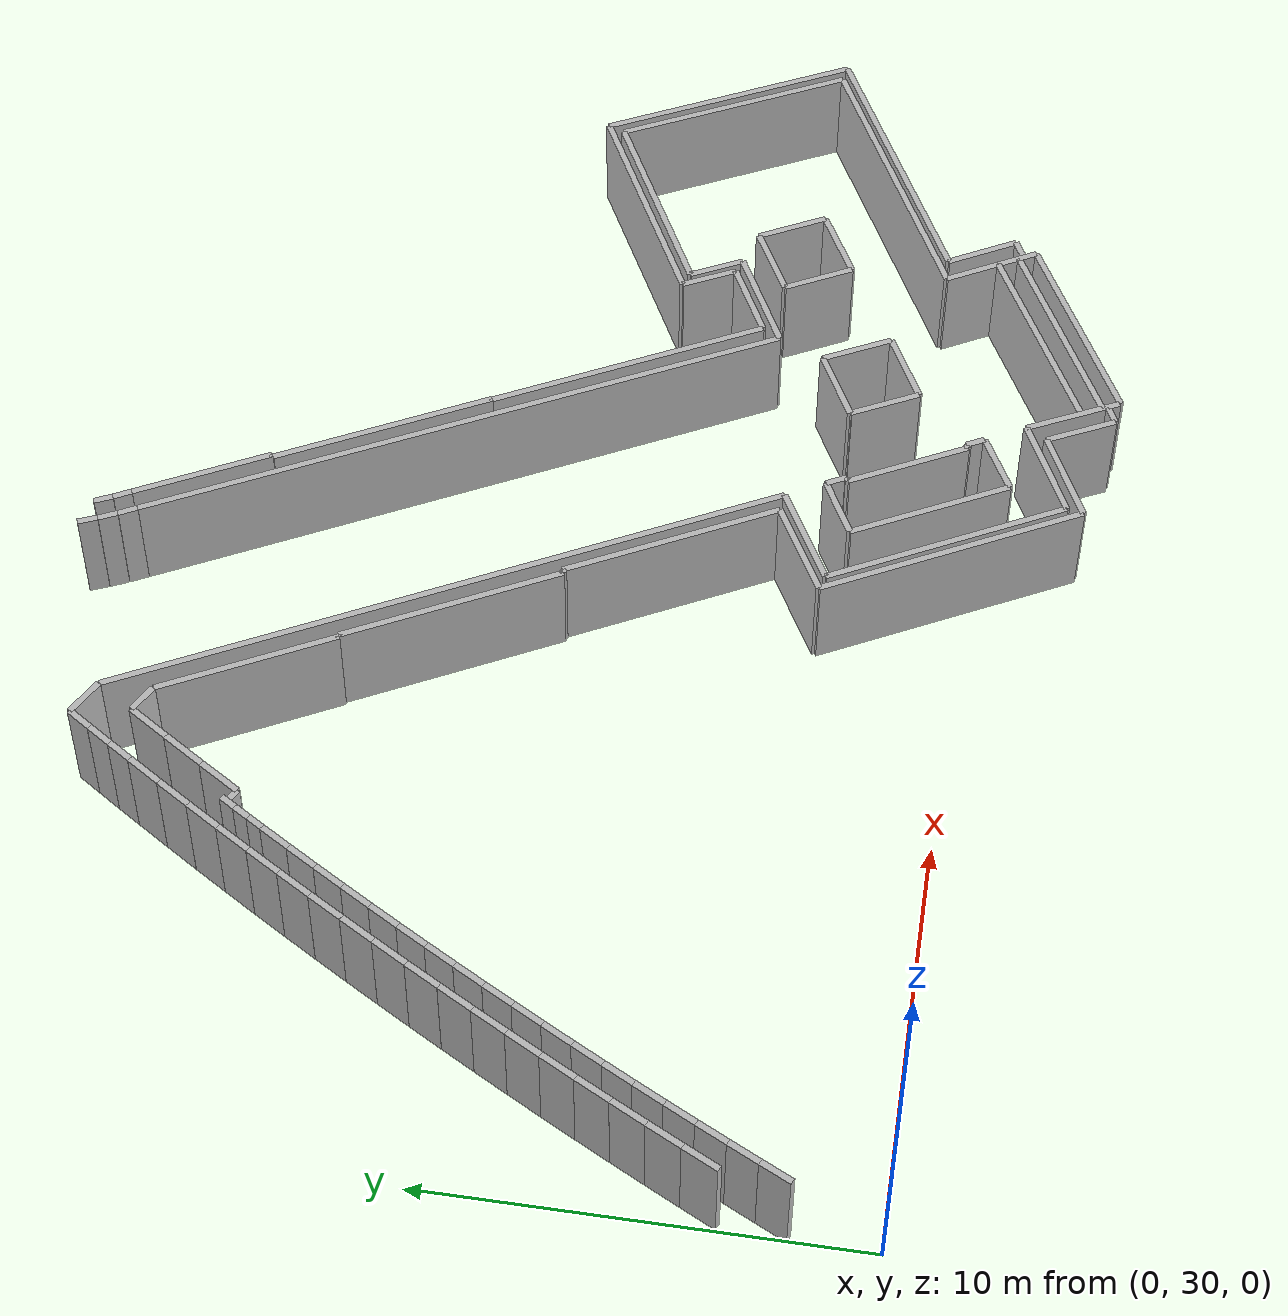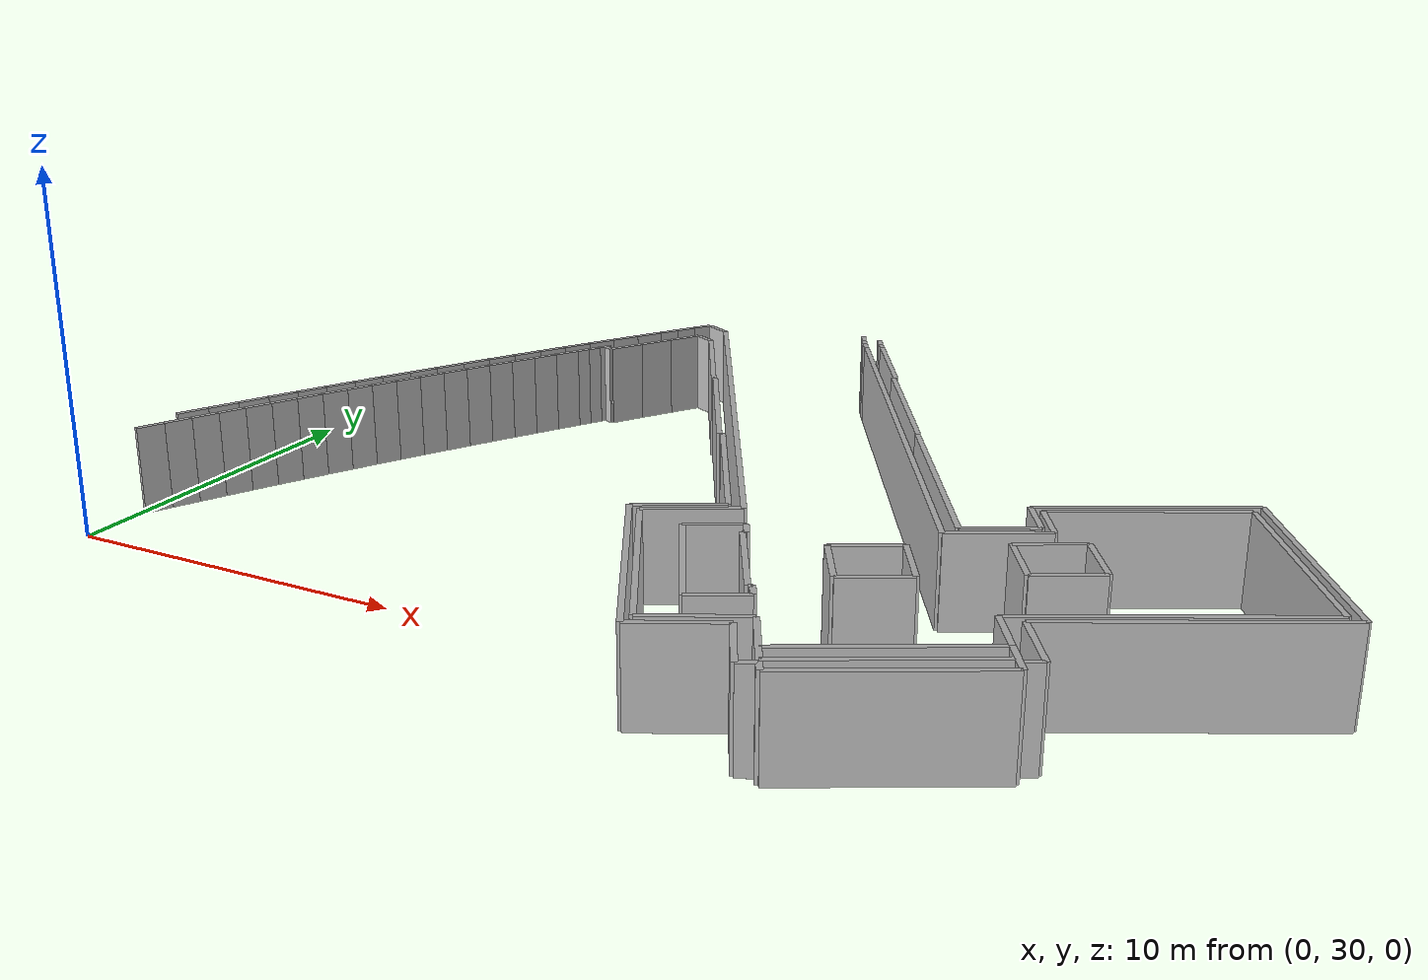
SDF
<?xml version="1.0" ?>
<sdf version="1.6">
  <model name="sps_0204">
    <pose frame="">0 0 0 0 -0 0</pose>
    <static>1</static>
    <self_collide>0</self_collide>
    <allow_auto_disable>0</allow_auto_disable>
    <link name="Wall28">
      <kinematic>0</kinematic>
      <gravity>1</gravity>
      <self_collide>0</self_collide>
      <collision name="collision">
        <geometry>
          <box>
            <size>4.25279 0.15 2.5</size>
          </box>
        </geometry>
        <pose frame="">0 0 0 0 -0 0</pose>
      </collision>
      <visual name="visual">
        <geometry>
          <box>
            <size>4.25279 0.15 2.5</size>
          </box>
        </geometry>
        <pose frame="">0 0 0 0 -0 0</pose>
        <cast_shadows>1</cast_shadows>
        <transparency>0.0</transparency>
      </visual>
      <pose frame="">11.0373 45.4844 1.25 0 -0 2.05709</pose>
    </link>
    <link name="Wall30">
      <kinematic>0</kinematic>
      <gravity>1</gravity>
      <self_collide>0</self_collide>
      <collision name="collision">
        <geometry>
          <box>
            <size>0.0966874 0.15 2.5</size>
          </box>
        </geometry>
        <pose frame="">0 0 0 0 -0 0</pose>
      </collision>
      <visual name="visual">
        <geometry>
          <box>
            <size>0.0966874 0.15 2.5</size>
          </box>
        </geometry>
        <pose frame="">0 0 0 0 -0 0</pose>
        <cast_shadows>1</cast_shadows>
        <transparency>0.0</transparency>
      </visual>
      <pose frame="">14.5934 38.9708 1.25 0 -0 0.474658</pose>
    </link>
    <link name="Wall33">
      <kinematic>0</kinematic>
      <gravity>1</gravity>
      <self_collide>0</self_collide>
      <collision name="collision">
        <geometry>
          <box>
            <size>6.47312 0.15 2.5</size>
          </box>
        </geometry>
        <pose frame="">0 0 0 0 -0 0</pose>
      </collision>
      <visual name="visual">
        <geometry>
          <box>
            <size>6.47312 0.15 2.5</size>
          </box>
        </geometry>
        <pose frame="">0 0 0 0 -0 0</pose>
        <cast_shadows>1</cast_shadows>
        <transparency>0.0</transparency>
      </visual>
      <pose frame="">16.5102 30.3436 1.25 0 0 -1.08328</pose>
    </link>
    <link name="Wall35">
      <kinematic>0</kinematic>
      <gravity>1</gravity>
      <self_collide>0</self_collide>
      <collision name="collision">
        <geometry>
          <box>
            <size>2.28858 0.15 2.5</size>
          </box>
        </geometry>
        <pose frame="">0 0 0 0 -0 0</pose>
      </collision>
      <visual name="visual">
        <geometry>
          <box>
            <size>2.28858 0.15 2.5</size>
          </box>
        </geometry>
        <pose frame="">0 0 0 0 -0 0</pose>
        <cast_shadows>1</cast_shadows>
        <transparency>0.0</transparency>
      </visual>
      <pose frame="">19.0546 27.9861 1.25 0 -0 0.454166</pose>
    </link>
    <link name="Wall413">
      <kinematic>0</kinematic>
      <gravity>1</gravity>
      <self_collide>0</self_collide>
      <collision name="collision">
        <geometry>
          <box>
            <size>2.34081 0.15 2.5</size>
          </box>
        </geometry>
        <pose frame="">0 0 0 0 -0 0</pose>
      </collision>
      <visual name="visual">
        <geometry>
          <box>
            <size>2.34081 0.15 2.5</size>
          </box>
        </geometry>
        <pose frame="">0 0 0 0 -0 0</pose>
        <cast_shadows>1</cast_shadows>
        <transparency>0.0</transparency>
      </visual>
      <pose frame="">20.8993 27.9341 1.25 0 0 -1.10477</pose>
    </link>
    <link name="Wall415">
      <kinematic>0</kinematic>
      <gravity>1</gravity>
      <self_collide>0</self_collide>
      <collision name="collision">
        <geometry>
          <box>
            <size>6.75894 0.15 2.5</size>
          </box>
        </geometry>
        <pose frame="">0 0 0 0 -0 0</pose>
      </collision>
      <visual name="visual">
        <geometry>
          <box>
            <size>6.75894 0.15 2.5</size>
          </box>
        </geometry>
        <pose frame="">0 0 0 0 -0 0</pose>
        <cast_shadows>1</cast_shadows>
        <transparency>0.0</transparency>
      </visual>
      <pose frame="">20.9337 38.4247 1.25 0 -0 2.05625</pose>
    </link>
    <link name="Wall416">
      <kinematic>0</kinematic>
      <gravity>1</gravity>
      <self_collide>0</self_collide>
      <collision name="collision">
        <geometry>
          <box>
            <size>4.99709 0.15 2.5</size>
          </box>
        </geometry>
        <pose frame="">0 0 0 0 -0 0</pose>
      </collision>
      <visual name="visual">
        <geometry>
          <box>
            <size>4.99709 0.15 2.5</size>
          </box>
        </geometry>
        <pose frame="">0 0 0 0 -0 0</pose>
        <cast_shadows>1</cast_shadows>
        <transparency>0.0</transparency>
      </visual>
      <pose frame="">23.6555 28.0325 1.25 0 -0 0.484067</pose>
    </link>
    <link name="Wall755">
      <kinematic>0</kinematic>
      <gravity>1</gravity>
      <self_collide>0</self_collide>
      <collision name="collision">
        <geometry>
          <box>
            <size>0.728258 0.15 2.5</size>
          </box>
        </geometry>
        <pose frame="">0 0 0 0 -0 0</pose>
      </collision>
      <visual name="visual">
        <geometry>
          <box>
            <size>0.728258 0.15 2.5</size>
          </box>
        </geometry>
        <pose frame="">0 0 0 0 -0 0</pose>
        <cast_shadows>1</cast_shadows>
        <transparency>0.0</transparency>
      </visual>
      <pose frame="">9.72488 47.5406 1.25 0 0 -0.505413</pose>
    </link>
    <link name="Wall759">
      <kinematic>0</kinematic>
      <gravity>1</gravity>
      <self_collide>0</self_collide>
      <collision name="collision">
        <geometry>
          <box>
            <size>5.32181 0.15 2.5</size>
          </box>
        </geometry>
        <pose frame="">0 0 0 0 -0 0</pose>
      </collision>
      <visual name="visual">
        <geometry>
          <box>
            <size>5.32181 0.15 2.5</size>
          </box>
        </geometry>
        <pose frame="">0 0 0 0 -0 0</pose>
        <cast_shadows>1</cast_shadows>
        <transparency>0.0</transparency>
      </visual>
      <pose frame="">18.1328 43.7763 1.25 0 -0 2.05629</pose>
    </link>
    <link name="Wall760">
      <kinematic>0</kinematic>
      <gravity>1</gravity>
      <self_collide>0</self_collide>
      <collision name="collision">
        <geometry>
          <box>
            <size>0.456406 0.15 2.5</size>
          </box>
        </geometry>
        <pose frame="">0 0 0 0 -0 0</pose>
      </collision>
      <visual name="visual">
        <geometry>
          <box>
            <size>0.456406 0.15 2.5</size>
          </box>
        </geometry>
        <pose frame="">0 0 0 0 -0 0</pose>
        <cast_shadows>1</cast_shadows>
        <transparency>0.0</transparency>
      </visual>
      <pose frame="">21.0629 27.0474 1.25 0 -0 0.454079</pose>
    </link>
    <link name="Wall762">
      <kinematic>0</kinematic>
      <gravity>1</gravity>
      <self_collide>0</self_collide>
      <collision name="collision">
        <geometry>
          <box>
            <size>1.93319 0.15 2.5</size>
          </box>
        </geometry>
        <pose frame="">0 0 0 0 -0 0</pose>
      </collision>
      <visual name="visual">
        <geometry>
          <box>
            <size>1.93319 0.15 2.5</size>
          </box>
        </geometry>
        <pose frame="">0 0 0 0 -0 0</pose>
        <cast_shadows>1</cast_shadows>
        <transparency>0.0</transparency>
      </visual>
      <pose frame="">23.3712 35.8758 1.25 0 0 -2.66888</pose>
    </link>
    <link name="Wall1157">
      <kinematic>0</kinematic>
      <gravity>1</gravity>
      <self_collide>0</self_collide>
      <collision name="collision">
        <geometry>
          <box>
            <size>3.35007 0.15 2.5</size>
          </box>
        </geometry>
        <pose frame="">0 0 0 0 -0 0</pose>
      </collision>
      <visual name="visual">
        <geometry>
          <box>
            <size>3.35007 0.15 2.5</size>
          </box>
        </geometry>
        <pose frame="">0 0 0 0 -0 0</pose>
        <cast_shadows>1</cast_shadows>
        <transparency>0.0</transparency>
      </visual>
      <pose frame="">16.1663 47.6404 1.25 0 -0 2.05625</pose>
    </link>
    <link name="Wall1159">
      <kinematic>0</kinematic>
      <gravity>1</gravity>
      <self_collide>0</self_collide>
      <collision name="collision">
        <geometry>
          <box>
            <size>0.0198736 0.15 2.5</size>
          </box>
        </geometry>
        <pose frame="">0 0 0 0 -0 0</pose>
      </collision>
      <visual name="visual">
        <geometry>
          <box>
            <size>0.0198736 0.15 2.5</size>
          </box>
        </geometry>
        <pose frame="">0 0 0 0 -0 0</pose>
        <cast_shadows>1</cast_shadows>
        <transparency>0.0</transparency>
      </visual>
      <pose frame="">19.3657 41.4183 1.25 0 -0 0.478756</pose>
    </link>
    <link name="Wall1162">
      <kinematic>0</kinematic>
      <gravity>1</gravity>
      <self_collide>0</self_collide>
      <collision name="collision">
        <geometry>
          <box>
            <size>4.98615 0.15 2.5</size>
          </box>
        </geometry>
        <pose frame="">0 0 0 0 -0 0</pose>
      </collision>
      <visual name="visual">
        <geometry>
          <box>
            <size>4.98615 0.15 2.5</size>
          </box>
        </geometry>
        <pose frame="">0 0 0 0 -0 0</pose>
        <cast_shadows>1</cast_shadows>
        <transparency>0.0</transparency>
      </visual>
      <pose frame="">23.1949 28.9172 1.25 0 -0 0.485913</pose>
    </link>
    <link name="Wall1165">
      <kinematic>0</kinematic>
      <gravity>1</gravity>
      <self_collide>0</self_collide>
      <collision name="collision">
        <geometry>
          <box>
            <size>5.58246 0.15 2.5</size>
          </box>
        </geometry>
        <pose frame="">0 0 0 0 -0 0</pose>
      </collision>
      <visual name="visual">
        <geometry>
          <box>
            <size>5.58246 0.15 2.5</size>
          </box>
        </geometry>
        <pose frame="">0 0 0 0 -0 0</pose>
        <cast_shadows>1</cast_shadows>
        <transparency>0.0</transparency>
      </visual>
      <pose frame="">26.1027 38.7876 1.25 0 0 -2.66886</pose>
    </link>
    <link name="Wall1166">
      <kinematic>0</kinematic>
      <gravity>1</gravity>
      <self_collide>0</self_collide>
      <collision name="collision">
        <geometry>
          <box>
            <size>6.91351 0.15 2.5</size>
          </box>
        </geometry>
        <pose frame="">0 0 0 0 -0 0</pose>
      </collision>
      <visual name="visual">
        <geometry>
          <box>
            <size>6.91351 0.15 2.5</size>
          </box>
        </geometry>
        <pose frame="">0 0 0 0 -0 0</pose>
        <cast_shadows>1</cast_shadows>
        <transparency>0.0</transparency>
      </visual>
      <pose frame="">28.391 32.8515 1.25 0 -0 0.472756</pose>
    </link>
    <link name="Wall1476">
      <kinematic>0</kinematic>
      <gravity>1</gravity>
      <self_collide>0</self_collide>
      <collision name="collision">
        <geometry>
          <box>
            <size>5.29302 0.15 2.5</size>
          </box>
        </geometry>
        <pose frame="">0 0 0 0 -0 0</pose>
      </collision>
      <visual name="visual">
        <geometry>
          <box>
            <size>5.29302 0.15 2.5</size>
          </box>
        </geometry>
        <pose frame="">0 0 0 0 -0 0</pose>
        <cast_shadows>1</cast_shadows>
        <transparency>0.0</transparency>
      </visual>
      <pose frame="">13.3136 41.2884 1.25 0 0 -1.08449</pose>
    </link>
    <link name="Wall1481">
      <kinematic>0</kinematic>
      <gravity>1</gravity>
      <self_collide>0</self_collide>
      <collision name="collision">
        <geometry>
          <box>
            <size>1.34765 0.15 2.5</size>
          </box>
        </geometry>
        <pose frame="">0 0 0 0 -0 0</pose>
      </collision>
      <visual name="visual">
        <geometry>
          <box>
            <size>1.34765 0.15 2.5</size>
          </box>
        </geometry>
        <pose frame="">0 0 0 0 -0 0</pose>
        <cast_shadows>1</cast_shadows>
        <transparency>0.0</transparency>
      </visual>
      <pose frame="">25.0743 30.6717 1.25 0 -0 2.07427</pose>
    </link>
    <link name="Wall1766">
      <kinematic>0</kinematic>
      <gravity>1</gravity>
      <self_collide>0</self_collide>
      <collision name="collision">
        <geometry>
          <box>
            <size>0.344899 0.15 2.5</size>
          </box>
        </geometry>
        <pose frame="">0 0 0 0 -0 0</pose>
      </collision>
      <visual name="visual">
        <geometry>
          <box>
            <size>0.344899 0.15 2.5</size>
          </box>
        </geometry>
        <pose frame="">0 0 0 0 -0 0</pose>
        <cast_shadows>1</cast_shadows>
        <transparency>0.0</transparency>
      </visual>
      <pose frame="">7.48968 45.0377 1.25 0 0 -0.453755</pose>
    </link>
    <link name="Wall1768">
      <kinematic>0</kinematic>
      <gravity>1</gravity>
      <self_collide>0</self_collide>
      <collision name="collision">
        <geometry>
          <box>
            <size>0.0513748 0.15 2.5</size>
          </box>
        </geometry>
        <pose frame="">0 0 0 0 -0 0</pose>
      </collision>
      <visual name="visual">
        <geometry>
          <box>
            <size>0.0513748 0.15 2.5</size>
          </box>
        </geometry>
        <pose frame="">0 0 0 0 -0 0</pose>
        <cast_shadows>1</cast_shadows>
        <transparency>0.0</transparency>
      </visual>
      <pose frame="">12.0539 43.6163 1.25 0 -0 0.476399</pose>
    </link>
    <link name="Wall2111">
      <kinematic>0</kinematic>
      <gravity>1</gravity>
      <self_collide>0</self_collide>
      <collision name="collision">
        <geometry>
          <box>
            <size>15.6909 0.15 2.5</size>
          </box>
        </geometry>
        <pose frame="">0 0 0 0 -0 0</pose>
      </collision>
      <visual name="visual">
        <geometry>
          <box>
            <size>15.6909 0.15 2.5</size>
          </box>
        </geometry>
        <pose frame="">0 0 0 0 -0 0</pose>
        <cast_shadows>1</cast_shadows>
        <transparency>0.0</transparency>
      </visual>
      <pose frame="">18.5987 41.9436 1.25 0 -0 2.05628</pose>
    </link>
    <link name="Wall2112">
      <kinematic>0</kinematic>
      <gravity>1</gravity>
      <self_collide>0</self_collide>
      <collision name="collision">
        <geometry>
          <box>
            <size>1.34877 0.15 2.5</size>
          </box>
        </geometry>
        <pose frame="">0 0 0 0 -0 0</pose>
      </collision>
      <visual name="visual">
        <geometry>
          <box>
            <size>1.34877 0.15 2.5</size>
          </box>
        </geometry>
        <pose frame="">0 0 0 0 -0 0</pose>
        <cast_shadows>1</cast_shadows>
        <transparency>0.0</transparency>
      </visual>
      <pose frame="">23.9247 36.9163 1.25 0 0 -1.098</pose>
    </link>
    <link name="Wall2115">
      <kinematic>0</kinematic>
      <gravity>1</gravity>
      <self_collide>0</self_collide>
      <collision name="collision">
        <geometry>
          <box>
            <size>1.0022 0.15 2.5</size>
          </box>
        </geometry>
        <pose frame="">0 0 0 0 -0 0</pose>
      </collision>
      <visual name="visual">
        <geometry>
          <box>
            <size>1.0022 0.15 2.5</size>
          </box>
        </geometry>
        <pose frame="">0 0 0 0 -0 0</pose>
        <cast_shadows>1</cast_shadows>
        <transparency>0.0</transparency>
      </visual>
      <pose frame="">25.6379 29.6408 1.25 0 0 -1.07476</pose>
    </link>
    <link name="Wall2116">
      <kinematic>0</kinematic>
      <gravity>1</gravity>
      <self_collide>0</self_collide>
      <collision name="collision">
        <geometry>
          <box>
            <size>0.506853 0.15 2.5</size>
          </box>
        </geometry>
        <pose frame="">0 0 0 0 -0 0</pose>
      </collision>
      <visual name="visual">
        <geometry>
          <box>
            <size>0.506853 0.15 2.5</size>
          </box>
        </geometry>
        <pose frame="">0 0 0 0 -0 0</pose>
        <cast_shadows>1</cast_shadows>
        <transparency>0.0</transparency>
      </visual>
      <pose frame="">25.946 29.6037 1.25 0 0 -2.66346</pose>
    </link>
    <link name="Wall2117">
      <kinematic>0</kinematic>
      <gravity>1</gravity>
      <self_collide>0</self_collide>
      <collision name="collision">
        <geometry>
          <box>
            <size>1.77773 0.15 2.5</size>
          </box>
        </geometry>
        <pose frame="">0 0 0 0 -0 0</pose>
      </collision>
      <visual name="visual">
        <geometry>
          <box>
            <size>1.77773 0.15 2.5</size>
          </box>
        </geometry>
        <pose frame="">0 0 0 0 -0 0</pose>
        <cast_shadows>1</cast_shadows>
        <transparency>0.0</transparency>
      </visual>
      <pose frame="">25.7422 30.4989 1.25 0 -0 2.07421</pose>
    </link>
    <link name="Wall2487">
      <kinematic>0</kinematic>
      <gravity>1</gravity>
      <self_collide>0</self_collide>
      <collision name="collision">
        <geometry>
          <box>
            <size>0.0638214 0.15 2.5</size>
          </box>
        </geometry>
        <pose frame="">0 0 0 0 -0 0</pose>
      </collision>
      <visual name="visual">
        <geometry>
          <box>
            <size>0.0638214 0.15 2.5</size>
          </box>
        </geometry>
        <pose frame="">0 0 0 0 -0 0</pose>
        <cast_shadows>1</cast_shadows>
        <transparency>0.0</transparency>
      </visual>
      <pose frame="">16.9195 46.1443 1.25 0 -0 0.474768</pose>
    </link>
    <link name="Wall2489">
      <kinematic>0</kinematic>
      <gravity>1</gravity>
      <self_collide>0</self_collide>
      <collision name="collision">
        <geometry>
          <box>
            <size>2.39007 0.15 2.5</size>
          </box>
        </geometry>
        <pose frame="">0 0 0 0 -0 0</pose>
      </collision>
      <visual name="visual">
        <geometry>
          <box>
            <size>2.39007 0.15 2.5</size>
          </box>
        </geometry>
        <pose frame="">0 0 0 0 -0 0</pose>
        <cast_shadows>1</cast_shadows>
        <transparency>0.0</transparency>
      </visual>
      <pose frame="">16.0427 33.7761 1.25 0 0 -2.64153</pose>
    </link>
    <link name="Wall2490">
      <kinematic>0</kinematic>
      <gravity>1</gravity>
      <self_collide>0</self_collide>
      <collision name="collision">
        <geometry>
          <box>
            <size>5.25281 0.15 2.5</size>
          </box>
        </geometry>
        <pose frame="">0 0 0 0 -0 0</pose>
      </collision>
      <visual name="visual">
        <geometry>
          <box>
            <size>5.25281 0.15 2.5</size>
          </box>
        </geometry>
        <pose frame="">0 0 0 0 -0 0</pose>
        <cast_shadows>1</cast_shadows>
        <transparency>0.0</transparency>
      </visual>
      <pose frame="">15.8639 36.671 1.25 0 0 -1.08448</pose>
    </link>
    <link name="Wall2493">
      <kinematic>0</kinematic>
      <gravity>1</gravity>
      <self_collide>0</self_collide>
      <collision name="collision">
        <geometry>
          <box>
            <size>1.72477 0.15 2.5</size>
          </box>
        </geometry>
        <pose frame="">0 0 0 0 -0 0</pose>
      </collision>
      <visual name="visual">
        <geometry>
          <box>
            <size>1.72477 0.15 2.5</size>
          </box>
        </geometry>
        <pose frame="">0 0 0 0 -0 0</pose>
        <cast_shadows>1</cast_shadows>
        <transparency>0.0</transparency>
      </visual>
      <pose frame="">20.4704 27.7177 1.25 0 0 -1.10476</pose>
    </link>
    <link name="Wall2496">
      <kinematic>0</kinematic>
      <gravity>1</gravity>
      <self_collide>0</self_collide>
      <collision name="collision">
        <geometry>
          <box>
            <size>4.99734 0.15 2.5</size>
          </box>
        </geometry>
        <pose frame="">0 0 0 0 -0 0</pose>
      </collision>
      <visual name="visual">
        <geometry>
          <box>
            <size>4.99734 0.15 2.5</size>
          </box>
        </geometry>
        <pose frame="">0 0 0 0 -0 0</pose>
        <cast_shadows>1</cast_shadows>
        <transparency>0.0</transparency>
      </visual>
      <pose frame="">23.4412 28.4403 1.25 0 -0 0.484055</pose>
    </link>
    <link name="Wall2502">
      <kinematic>0</kinematic>
      <gravity>1</gravity>
      <self_collide>0</self_collide>
      <collision name="collision">
        <geometry>
          <box>
            <size>6.3269 0.15 2.5</size>
          </box>
        </geometry>
        <pose frame="">0 0 0 0 -0 0</pose>
      </collision>
      <visual name="visual">
        <geometry>
          <box>
            <size>6.3269 0.15 2.5</size>
          </box>
        </geometry>
        <pose frame="">0 0 0 0 -0 0</pose>
        <cast_shadows>1</cast_shadows>
        <transparency>0.0</transparency>
      </visual>
      <pose frame="">30.0283 37.242 1.25 0 -0 2.04353</pose>
    </link>
    <link name="Wall6495">
      <kinematic>0</kinematic>
      <gravity>1</gravity>
      <self_collide>0</self_collide>
      <collision name="collision">
        <geometry>
          <box>
            <size>1.72361 0.15 2.5</size>
          </box>
        </geometry>
        <pose frame="">0 0 0 0 -0 0</pose>
      </collision>
      <visual name="visual">
        <geometry>
          <box>
            <size>1.72361 0.15 2.5</size>
          </box>
        </geometry>
        <pose frame="">0 0 0 0 -0 0</pose>
        <cast_shadows>1</cast_shadows>
        <transparency>0.0</transparency>
      </visual>
      <pose frame="">24.2963 34.3156 1.25 0 0 -1.08353</pose>
    </link>
    <link name="Wall6496">
      <kinematic>0</kinematic>
      <gravity>1</gravity>
      <self_collide>0</self_collide>
      <collision name="collision">
        <geometry>
          <box>
            <size>1.76609 0.15 2.5</size>
          </box>
        </geometry>
        <pose frame="">0 0 0 0 -0 0</pose>
      </collision>
      <visual name="visual">
        <geometry>
          <box>
            <size>1.76609 0.15 2.5</size>
          </box>
        </geometry>
        <pose frame="">0 0 0 0 -0 0</pose>
        <cast_shadows>1</cast_shadows>
        <transparency>0.0</transparency>
      </visual>
      <pose frame="">25.4802 33.9675 1.25 0 -0 0.487188</pose>
    </link>
    <link name="Wall6497">
      <kinematic>0</kinematic>
      <gravity>1</gravity>
      <self_collide>0</self_collide>
      <collision name="collision">
        <geometry>
          <box>
            <size>1.72369 0.15 2.5</size>
          </box>
        </geometry>
        <pose frame="">0 0 0 0 -0 0</pose>
      </collision>
      <visual name="visual">
        <geometry>
          <box>
            <size>1.72369 0.15 2.5</size>
          </box>
        </geometry>
        <pose frame="">0 0 0 0 -0 0</pose>
        <cast_shadows>1</cast_shadows>
        <transparency>0.0</transparency>
      </visual>
      <pose frame="">25.8569 35.1424 1.25 0 -0 2.05815</pose>
    </link>
    <link name="Wall6498">
      <kinematic>0</kinematic>
      <gravity>1</gravity>
      <self_collide>0</self_collide>
      <collision name="collision">
        <geometry>
          <box>
            <size>1.76593 0.15 2.5</size>
          </box>
        </geometry>
        <pose frame="">0 0 0 0 -0 0</pose>
      </collision>
      <visual name="visual">
        <geometry>
          <box>
            <size>1.76593 0.15 2.5</size>
          </box>
        </geometry>
        <pose frame="">0 0 0 0 -0 0</pose>
        <cast_shadows>1</cast_shadows>
        <transparency>0.0</transparency>
      </visual>
      <pose frame="">24.6731 35.4905 1.25 0 0 -2.65436</pose>
    </link>
    <link name="Wall8995">
      <kinematic>0</kinematic>
      <gravity>1</gravity>
      <self_collide>0</self_collide>
      <collision name="collision">
        <geometry>
          <box>
            <size>0.637463 0.15 2.5</size>
          </box>
        </geometry>
        <pose frame="">0 0 0 0 -0 0</pose>
      </collision>
      <visual name="visual">
        <geometry>
          <box>
            <size>0.637463 0.15 2.5</size>
          </box>
        </geometry>
        <pose frame="">0 0 0 0 -0 0</pose>
        <cast_shadows>1</cast_shadows>
        <transparency>0.0</transparency>
      </visual>
      <pose frame="">8.97726 48.7729 1.25 0 0 -2.15657</pose>
    </link>
    <link name="Wall8996">
      <kinematic>0</kinematic>
      <gravity>1</gravity>
      <self_collide>0</self_collide>
      <collision name="collision">
        <geometry>
          <box>
            <size>0.637495 0.15 2.5</size>
          </box>
        </geometry>
        <pose frame="">0 0 0 0 -0 0</pose>
      </collision>
      <visual name="visual">
        <geometry>
          <box>
            <size>0.637495 0.15 2.5</size>
          </box>
        </geometry>
        <pose frame="">0 0 0 0 -0 0</pose>
        <cast_shadows>1</cast_shadows>
        <transparency>0.0</transparency>
      </visual>
      <pose frame="">8.62615 48.2408 1.25 0 0 -2.1516</pose>
    </link>
    <link name="Wall8997">
      <kinematic>0</kinematic>
      <gravity>1</gravity>
      <self_collide>0</self_collide>
      <collision name="collision">
        <geometry>
          <box>
            <size>0.637545 0.15 2.5</size>
          </box>
        </geometry>
        <pose frame="">0 0 0 0 -0 0</pose>
      </collision>
      <visual name="visual">
        <geometry>
          <box>
            <size>0.637545 0.15 2.5</size>
          </box>
        </geometry>
        <pose frame="">0 0 0 0 -0 0</pose>
        <cast_shadows>1</cast_shadows>
        <transparency>0.0</transparency>
      </visual>
      <pose frame="">8.27776 47.7069 1.25 0 0 -2.14629</pose>
    </link>
    <link name="Wall8998">
      <kinematic>0</kinematic>
      <gravity>1</gravity>
      <self_collide>0</self_collide>
      <collision name="collision">
        <geometry>
          <box>
            <size>0.895615 0.15 2.5</size>
          </box>
        </geometry>
        <pose frame="">0 0 0 0 -0 0</pose>
      </collision>
      <visual name="visual">
        <geometry>
          <box>
            <size>0.895615 0.15 2.5</size>
          </box>
        </geometry>
        <pose frame="">0 0 0 0 -0 0</pose>
        <cast_shadows>1</cast_shadows>
        <transparency>0.0</transparency>
      </visual>
      <pose frame="">7.86196 47.0629 1.25 0 0 -2.14254</pose>
    </link>
    <link name="Wall8999">
      <kinematic>0</kinematic>
      <gravity>1</gravity>
      <self_collide>0</self_collide>
      <collision name="collision">
        <geometry>
          <box>
            <size>0.895689 0.15 2.5</size>
          </box>
        </geometry>
        <pose frame="">0 0 0 0 -0 0</pose>
      </collision>
      <visual name="visual">
        <geometry>
          <box>
            <size>0.895689 0.15 2.5</size>
          </box>
        </geometry>
        <pose frame="">0 0 0 0 -0 0</pose>
        <cast_shadows>1</cast_shadows>
        <transparency>0.0</transparency>
      </visual>
      <pose frame="">7.37966 46.3082 1.25 0 0 -2.13634</pose>
    </link>
    <link name="Wall9000">
      <kinematic>0</kinematic>
      <gravity>1</gravity>
      <self_collide>0</self_collide>
      <collision name="collision">
        <geometry>
          <box>
            <size>0.895531 0.15 2.5</size>
          </box>
        </geometry>
        <pose frame="">0 0 0 0 -0 0</pose>
      </collision>
      <visual name="visual">
        <geometry>
          <box>
            <size>0.895531 0.15 2.5</size>
          </box>
        </geometry>
        <pose frame="">0 0 0 0 -0 0</pose>
        <cast_shadows>1</cast_shadows>
        <transparency>0.0</transparency>
      </visual>
      <pose frame="">6.90215 45.5505 1.25 0 0 -2.12993</pose>
    </link>
    <link name="Wall9001">
      <kinematic>0</kinematic>
      <gravity>1</gravity>
      <self_collide>0</self_collide>
      <collision name="collision">
        <geometry>
          <box>
            <size>0.895547 0.15 2.5</size>
          </box>
        </geometry>
        <pose frame="">0 0 0 0 -0 0</pose>
      </collision>
      <visual name="visual">
        <geometry>
          <box>
            <size>0.895547 0.15 2.5</size>
          </box>
        </geometry>
        <pose frame="">0 0 0 0 -0 0</pose>
        <cast_shadows>1</cast_shadows>
        <transparency>0.0</transparency>
      </visual>
      <pose frame="">6.42956 44.7898 1.25 0 0 -2.1235</pose>
    </link>
    <link name="Wall9002">
      <kinematic>0</kinematic>
      <gravity>1</gravity>
      <self_collide>0</self_collide>
      <collision name="collision">
        <geometry>
          <box>
            <size>0.895642 0.15 2.5</size>
          </box>
        </geometry>
        <pose frame="">0 0 0 0 -0 0</pose>
      </collision>
      <visual name="visual">
        <geometry>
          <box>
            <size>0.895642 0.15 2.5</size>
          </box>
        </geometry>
        <pose frame="">0 0 0 0 -0 0</pose>
        <cast_shadows>1</cast_shadows>
        <transparency>0.0</transparency>
      </visual>
      <pose frame="">5.96175 44.0261 1.25 0 0 -2.11728</pose>
    </link>
    <link name="Wall9003">
      <kinematic>0</kinematic>
      <gravity>1</gravity>
      <self_collide>0</self_collide>
      <collision name="collision">
        <geometry>
          <box>
            <size>0.895521 0.15 2.5</size>
          </box>
        </geometry>
        <pose frame="">0 0 0 0 -0 0</pose>
      </collision>
      <visual name="visual">
        <geometry>
          <box>
            <size>0.895521 0.15 2.5</size>
          </box>
        </geometry>
        <pose frame="">0 0 0 0 -0 0</pose>
        <cast_shadows>1</cast_shadows>
        <transparency>0.0</transparency>
      </visual>
      <pose frame="">5.49874 43.2595 1.25 0 0 -2.11099</pose>
    </link>
    <link name="Wall9004">
      <kinematic>0</kinematic>
      <gravity>1</gravity>
      <self_collide>0</self_collide>
      <collision name="collision">
        <geometry>
          <box>
            <size>0.895498 0.15 2.5</size>
          </box>
        </geometry>
        <pose frame="">0 0 0 0 -0 0</pose>
      </collision>
      <visual name="visual">
        <geometry>
          <box>
            <size>0.895498 0.15 2.5</size>
          </box>
        </geometry>
        <pose frame="">0 0 0 0 -0 0</pose>
        <cast_shadows>1</cast_shadows>
        <transparency>0.0</transparency>
      </visual>
      <pose frame="">5.04055 42.4901 1.25 0 0 -2.10482</pose>
    </link>
    <link name="Wall9005">
      <kinematic>0</kinematic>
      <gravity>1</gravity>
      <self_collide>0</self_collide>
      <collision name="collision">
        <geometry>
          <box>
            <size>0.895636 0.15 2.5</size>
          </box>
        </geometry>
        <pose frame="">0 0 0 0 -0 0</pose>
      </collision>
      <visual name="visual">
        <geometry>
          <box>
            <size>0.895636 0.15 2.5</size>
          </box>
        </geometry>
        <pose frame="">0 0 0 0 -0 0</pose>
        <cast_shadows>1</cast_shadows>
        <transparency>0.0</transparency>
      </visual>
      <pose frame="">4.58715 41.7178 1.25 0 0 -2.09849</pose>
    </link>
    <link name="Wall9006">
      <kinematic>0</kinematic>
      <gravity>1</gravity>
      <self_collide>0</self_collide>
      <collision name="collision">
        <geometry>
          <box>
            <size>0.895559 0.15 2.5</size>
          </box>
        </geometry>
        <pose frame="">0 0 0 0 -0 0</pose>
      </collision>
      <visual name="visual">
        <geometry>
          <box>
            <size>0.895559 0.15 2.5</size>
          </box>
        </geometry>
        <pose frame="">0 0 0 0 -0 0</pose>
        <cast_shadows>1</cast_shadows>
        <transparency>0.0</transparency>
      </visual>
      <pose frame="">4.13866 40.9426 1.25 0 0 -2.09208</pose>
    </link>
    <link name="Wall9007">
      <kinematic>0</kinematic>
      <gravity>1</gravity>
      <self_collide>0</self_collide>
      <collision name="collision">
        <geometry>
          <box>
            <size>0.895428 0.15 2.5</size>
          </box>
        </geometry>
        <pose frame="">0 0 0 0 -0 0</pose>
      </collision>
      <visual name="visual">
        <geometry>
          <box>
            <size>0.895428 0.15 2.5</size>
          </box>
        </geometry>
        <pose frame="">0 0 0 0 -0 0</pose>
        <cast_shadows>1</cast_shadows>
        <transparency>0.0</transparency>
      </visual>
      <pose frame="">3.69506 40.1647 1.25 0 0 -2.08604</pose>
    </link>
    <link name="Wall9008">
      <kinematic>0</kinematic>
      <gravity>1</gravity>
      <self_collide>0</self_collide>
      <collision name="collision">
        <geometry>
          <box>
            <size>0.895637 0.15 2.5</size>
          </box>
        </geometry>
        <pose frame="">0 0 0 0 -0 0</pose>
      </collision>
      <visual name="visual">
        <geometry>
          <box>
            <size>0.895637 0.15 2.5</size>
          </box>
        </geometry>
        <pose frame="">0 0 0 0 -0 0</pose>
        <cast_shadows>1</cast_shadows>
        <transparency>0.0</transparency>
      </visual>
      <pose frame="">3.25634 39.384 1.25 0 0 -2.0795</pose>
    </link>
    <link name="Wall9009">
      <kinematic>0</kinematic>
      <gravity>1</gravity>
      <self_collide>0</self_collide>
      <collision name="collision">
        <geometry>
          <box>
            <size>0.895544 0.15 2.5</size>
          </box>
        </geometry>
        <pose frame="">0 0 0 0 -0 0</pose>
      </collision>
      <visual name="visual">
        <geometry>
          <box>
            <size>0.895544 0.15 2.5</size>
          </box>
        </geometry>
        <pose frame="">0 0 0 0 -0 0</pose>
        <cast_shadows>1</cast_shadows>
        <transparency>0.0</transparency>
      </visual>
      <pose frame="">2.82253 38.6005 1.25 0 0 -2.07341</pose>
    </link>
    <link name="Wall9010">
      <kinematic>0</kinematic>
      <gravity>1</gravity>
      <self_collide>0</self_collide>
      <collision name="collision">
        <geometry>
          <box>
            <size>0.895611 0.15 2.5</size>
          </box>
        </geometry>
        <pose frame="">0 0 0 0 -0 0</pose>
      </collision>
      <visual name="visual">
        <geometry>
          <box>
            <size>0.895611 0.15 2.5</size>
          </box>
        </geometry>
        <pose frame="">0 0 0 0 -0 0</pose>
        <cast_shadows>1</cast_shadows>
        <transparency>0.0</transparency>
      </visual>
      <pose frame="">2.39364 37.8143 1.25 0 0 -2.067</pose>
    </link>
    <link name="Wall9011">
      <kinematic>0</kinematic>
      <gravity>1</gravity>
      <self_collide>0</self_collide>
      <collision name="collision">
        <geometry>
          <box>
            <size>0.895554 0.15 2.5</size>
          </box>
        </geometry>
        <pose frame="">0 0 0 0 -0 0</pose>
      </collision>
      <visual name="visual">
        <geometry>
          <box>
            <size>0.895554 0.15 2.5</size>
          </box>
        </geometry>
        <pose frame="">0 0 0 0 -0 0</pose>
        <cast_shadows>1</cast_shadows>
        <transparency>0.0</transparency>
      </visual>
      <pose frame="">1.96975 37.0254 1.25 0 0 -2.06069</pose>
    </link>
    <link name="Wall9012">
      <kinematic>0</kinematic>
      <gravity>1</gravity>
      <self_collide>0</self_collide>
      <collision name="collision">
        <geometry>
          <box>
            <size>0.895641 0.15 2.5</size>
          </box>
        </geometry>
        <pose frame="">0 0 0 0 -0 0</pose>
      </collision>
      <visual name="visual">
        <geometry>
          <box>
            <size>0.895641 0.15 2.5</size>
          </box>
        </geometry>
        <pose frame="">0 0 0 0 -0 0</pose>
        <cast_shadows>1</cast_shadows>
        <transparency>0.0</transparency>
      </visual>
      <pose frame="">1.55086 36.2338 1.25 0 0 -2.05432</pose>
    </link>
    <link name="Wall9013">
      <kinematic>0</kinematic>
      <gravity>1</gravity>
      <self_collide>0</self_collide>
      <collision name="collision">
        <geometry>
          <box>
            <size>0.895521 0.15 2.5</size>
          </box>
        </geometry>
        <pose frame="">0 0 0 0 -0 0</pose>
      </collision>
      <visual name="visual">
        <geometry>
          <box>
            <size>0.895521 0.15 2.5</size>
          </box>
        </geometry>
        <pose frame="">0 0 0 0 -0 0</pose>
        <cast_shadows>1</cast_shadows>
        <transparency>0.0</transparency>
      </visual>
      <pose frame="">1.13695 35.4396 1.25 0 0 -2.04816</pose>
    </link>
    <link name="Wall9014">
      <kinematic>0</kinematic>
      <gravity>1</gravity>
      <self_collide>0</self_collide>
      <collision name="collision">
        <geometry>
          <box>
            <size>0.895489 0.15 2.5</size>
          </box>
        </geometry>
        <pose frame="">0 0 0 0 -0 0</pose>
      </collision>
      <visual name="visual">
        <geometry>
          <box>
            <size>0.895489 0.15 2.5</size>
          </box>
        </geometry>
        <pose frame="">0 0 0 0 -0 0</pose>
        <cast_shadows>1</cast_shadows>
        <transparency>0.0</transparency>
      </visual>
      <pose frame="">0.72805 34.6429 1.25 0 0 -2.04182</pose>
    </link>
    <link name="Wall9015">
      <kinematic>0</kinematic>
      <gravity>1</gravity>
      <self_collide>0</self_collide>
      <collision name="collision">
        <geometry>
          <box>
            <size>0.895601 0.15 2.5</size>
          </box>
        </geometry>
        <pose frame="">0 0 0 0 -0 0</pose>
      </collision>
      <visual name="visual">
        <geometry>
          <box>
            <size>0.895601 0.15 2.5</size>
          </box>
        </geometry>
        <pose frame="">0 0 0 0 -0 0</pose>
        <cast_shadows>1</cast_shadows>
        <transparency>0.0</transparency>
      </visual>
      <pose frame="">0.324149 33.8436 1.25 0 0 -2.03557</pose>
    </link>
    <link name="Wall9028">
      <kinematic>0</kinematic>
      <gravity>1</gravity>
      <self_collide>0</self_collide>
      <collision name="collision">
        <geometry>
          <box>
            <size>1.09009 0.15 2.5</size>
          </box>
        </geometry>
        <pose frame="">0 0 0 0 -0 0</pose>
      </collision>
      <visual name="visual">
        <geometry>
          <box>
            <size>1.09009 0.15 2.5</size>
          </box>
        </geometry>
        <pose frame="">0 0 0 0 -0 0</pose>
        <cast_shadows>1</cast_shadows>
        <transparency>0.0</transparency>
      </visual>
      <pose frame="">9.10967 47.2596 1.25 0 0 -2.1462</pose>
    </link>
    <link name="Wall9029">
      <kinematic>0</kinematic>
      <gravity>1</gravity>
      <self_collide>0</self_collide>
      <collision name="collision">
        <geometry>
          <box>
            <size>1.08977 0.15 2.5</size>
          </box>
        </geometry>
        <pose frame="">0 0 0 0 -0 0</pose>
      </collision>
      <visual name="visual">
        <geometry>
          <box>
            <size>1.08977 0.15 2.5</size>
          </box>
        </geometry>
        <pose frame="">0 0 0 0 -0 0</pose>
        <cast_shadows>1</cast_shadows>
        <transparency>0.0</transparency>
      </visual>
      <pose frame="">8.51946 46.3433 1.25 0 0 -2.13986</pose>
    </link>
    <link name="Wall9030">
      <kinematic>0</kinematic>
      <gravity>1</gravity>
      <self_collide>0</self_collide>
      <collision name="collision">
        <geometry>
          <box>
            <size>1.09001 0.15 2.5</size>
          </box>
        </geometry>
        <pose frame="">0 0 0 0 -0 0</pose>
      </collision>
      <visual name="visual">
        <geometry>
          <box>
            <size>1.09001 0.15 2.5</size>
          </box>
        </geometry>
        <pose frame="">0 0 0 0 -0 0</pose>
        <cast_shadows>1</cast_shadows>
        <transparency>0.0</transparency>
      </visual>
      <pose frame="">7.93514 45.4233 1.25 0 0 -2.13342</pose>
    </link>
    <link name="Wall9043">
      <kinematic>0</kinematic>
      <gravity>1</gravity>
      <self_collide>0</self_collide>
      <collision name="collision">
        <geometry>
          <box>
            <size>0.467468 0.15 2.5</size>
          </box>
        </geometry>
        <pose frame="">0 0 0 0 -0 0</pose>
      </collision>
      <visual name="visual">
        <geometry>
          <box>
            <size>0.467468 0.15 2.5</size>
          </box>
        </geometry>
        <pose frame="">0 0 0 0 -0 0</pose>
        <cast_shadows>1</cast_shadows>
        <transparency>0.0</transparency>
      </visual>
      <pose frame="">14.4293 49.9343 1.25 0 0 -1.1764</pose>
    </link>
    <link name="Wall9044">
      <kinematic>0</kinematic>
      <gravity>1</gravity>
      <self_collide>0</self_collide>
      <collision name="collision">
        <geometry>
          <box>
            <size>0.467509 0.15 2.5</size>
          </box>
        </geometry>
        <pose frame="">0 0 0 0 -0 0</pose>
      </collision>
      <visual name="visual">
        <geometry>
          <box>
            <size>0.467509 0.15 2.5</size>
          </box>
        </geometry>
        <pose frame="">0 0 0 0 -0 0</pose>
        <cast_shadows>1</cast_shadows>
        <transparency>0.0</transparency>
      </visual>
      <pose frame="">14.6188 49.5071 1.25 0 0 -1.13015</pose>
    </link>
    <link name="Wall9045">
      <kinematic>0</kinematic>
      <gravity>1</gravity>
      <self_collide>0</self_collide>
      <collision name="collision">
        <geometry>
          <box>
            <size>0.467685 0.15 2.5</size>
          </box>
        </geometry>
        <pose frame="">0 0 0 0 -0 0</pose>
      </collision>
      <visual name="visual">
        <geometry>
          <box>
            <size>0.467685 0.15 2.5</size>
          </box>
        </geometry>
        <pose frame="">0 0 0 0 -0 0</pose>
        <cast_shadows>1</cast_shadows>
        <transparency>0.0</transparency>
      </visual>
      <pose frame="">14.8281 49.0891 1.25 0 0 -1.08304</pose>
    </link>
    <link name="Wall12735">
      <kinematic>0</kinematic>
      <gravity>1</gravity>
      <self_collide>0</self_collide>
      <collision name="collision">
        <geometry>
          <box>
            <size>1.71909 0.15 2.5</size>
          </box>
        </geometry>
        <pose frame="">0 0 0 0 -0 0</pose>
      </collision>
      <visual name="visual">
        <geometry>
          <box>
            <size>1.71909 0.15 2.5</size>
          </box>
        </geometry>
        <pose frame="">0 0 0 0 -0 0</pose>
        <cast_shadows>1</cast_shadows>
        <transparency>0.0</transparency>
      </visual>
      <pose frame="">20.6027 32.3137 1.25 0 0 -1.09229</pose>
    </link>
    <link name="Wall12736">
      <kinematic>0</kinematic>
      <gravity>1</gravity>
      <self_collide>0</self_collide>
      <collision name="collision">
        <geometry>
          <box>
            <size>1.78818 0.15 2.5</size>
          </box>
        </geometry>
        <pose frame="">0 0 0 0 -0 0</pose>
      </collision>
      <visual name="visual">
        <geometry>
          <box>
            <size>1.78818 0.15 2.5</size>
          </box>
        </geometry>
        <pose frame="">0 0 0 0 -0 0</pose>
        <cast_shadows>1</cast_shadows>
        <transparency>0.0</transparency>
      </visual>
      <pose frame="">21.792 31.9625 1.25 0 -0 0.478653</pose>
    </link>
    <link name="Wall12737">
      <kinematic>0</kinematic>
      <gravity>1</gravity>
      <self_collide>0</self_collide>
      <collision name="collision">
        <geometry>
          <box>
            <size>1.73085 0.15 2.5</size>
          </box>
        </geometry>
        <pose frame="">0 0 0 0 -0 0</pose>
      </collision>
      <visual name="visual">
        <geometry>
          <box>
            <size>1.73085 0.15 2.5</size>
          </box>
        </geometry>
        <pose frame="">0 0 0 0 -0 0</pose>
        <cast_shadows>1</cast_shadows>
        <transparency>0.0</transparency>
      </visual>
      <pose frame="">22.1872 33.1425 1.25 0 -0 2.04932</pose>
    </link>
    <link name="Wall12738">
      <kinematic>0</kinematic>
      <gravity>1</gravity>
      <self_collide>0</self_collide>
      <collision name="collision">
        <geometry>
          <box>
            <size>1.7881 0.15 2.5</size>
          </box>
        </geometry>
        <pose frame="">0 0 0 0 -0 0</pose>
      </collision>
      <visual name="visual">
        <geometry>
          <box>
            <size>1.7881 0.15 2.5</size>
          </box>
        </geometry>
        <pose frame="">0 0 0 0 -0 0</pose>
        <cast_shadows>1</cast_shadows>
        <transparency>0.0</transparency>
      </visual>
      <pose frame="">20.995 33.499 1.25 0 0 -2.66303</pose>
    </link>
    <link name="Wall12739">
      <kinematic>0</kinematic>
      <gravity>1</gravity>
      <self_collide>0</self_collide>
      <collision name="collision">
        <geometry>
          <box>
            <size>0.0119287 0.15 2.5</size>
          </box>
        </geometry>
        <pose frame="">0 0 0 0 -0 0</pose>
      </collision>
      <visual name="visual">
        <geometry>
          <box>
            <size>0.0119287 0.15 2.5</size>
          </box>
        </geometry>
        <pose frame="">0 0 0 0 -0 0</pose>
        <cast_shadows>1</cast_shadows>
        <transparency>0.0</transparency>
      </visual>
      <pose frame="">20.2042 33.082 1.25 0 0 -1.098</pose>
    </link>
    <link name="Wall16542">
      <kinematic>0</kinematic>
      <gravity>1</gravity>
      <self_collide>0</self_collide>
      <collision name="collision">
        <geometry>
          <box>
            <size>0.401336 0.15 2.5</size>
          </box>
        </geometry>
        <pose frame="">0 0 0 0 -0 0</pose>
      </collision>
      <visual name="visual">
        <geometry>
          <box>
            <size>0.401336 0.15 2.5</size>
          </box>
        </geometry>
        <pose frame="">0 0 0 0 -0 0</pose>
        <cast_shadows>1</cast_shadows>
        <transparency>0.0</transparency>
      </visual>
      <pose frame="">7.31994 45.0896 1.25 0 0 -2.12796</pose>
    </link>
    <link name="Wall16543">
      <kinematic>0</kinematic>
      <gravity>1</gravity>
      <self_collide>0</self_collide>
      <collision name="collision">
        <geometry>
          <box>
            <size>0.401048 0.15 2.5</size>
          </box>
        </geometry>
        <pose frame="">0 0 0 0 -0 0</pose>
      </collision>
      <visual name="visual">
        <geometry>
          <box>
            <size>0.401048 0.15 2.5</size>
          </box>
        </geometry>
        <pose frame="">0 0 0 0 -0 0</pose>
        <cast_shadows>1</cast_shadows>
        <transparency>0.0</transparency>
      </visual>
      <pose frame="">7.10824 44.7488 1.25 0 0 -2.12536</pose>
    </link>
    <link name="Wall16544">
      <kinematic>0</kinematic>
      <gravity>1</gravity>
      <self_collide>0</self_collide>
      <collision name="collision">
        <geometry>
          <box>
            <size>0.401202 0.15 2.5</size>
          </box>
        </geometry>
        <pose frame="">0 0 0 0 -0 0</pose>
      </collision>
      <visual name="visual">
        <geometry>
          <box>
            <size>0.401202 0.15 2.5</size>
          </box>
        </geometry>
        <pose frame="">0 0 0 0 -0 0</pose>
        <cast_shadows>1</cast_shadows>
        <transparency>0.0</transparency>
      </visual>
      <pose frame="">6.89745 44.4075 1.25 0 0 -2.1228</pose>
    </link>
    <link name="Wall16545">
      <kinematic>0</kinematic>
      <gravity>1</gravity>
      <self_collide>0</self_collide>
      <collision name="collision">
        <geometry>
          <box>
            <size>0.778182 0.15 2.5</size>
          </box>
        </geometry>
        <pose frame="">0 0 0 0 -0 0</pose>
      </collision>
      <visual name="visual">
        <geometry>
          <box>
            <size>0.778182 0.15 2.5</size>
          </box>
        </geometry>
        <pose frame="">0 0 0 0 -0 0</pose>
        <cast_shadows>1</cast_shadows>
        <transparency>0.0</transparency>
      </visual>
      <pose frame="">6.58956 43.9046 1.25 0 0 -2.11876</pose>
    </link>
    <link name="Wall16546">
      <kinematic>0</kinematic>
      <gravity>1</gravity>
      <self_collide>0</self_collide>
      <collision name="collision">
        <geometry>
          <box>
            <size>0.778236 0.15 2.5</size>
          </box>
        </geometry>
        <pose frame="">0 0 0 0 -0 0</pose>
      </collision>
      <visual name="visual">
        <geometry>
          <box>
            <size>0.778236 0.15 2.5</size>
          </box>
        </geometry>
        <pose frame="">0 0 0 0 -0 0</pose>
        <cast_shadows>1</cast_shadows>
        <transparency>0.0</transparency>
      </visual>
      <pose frame="">6.18587 43.2393 1.25 0 0 -2.11358</pose>
    </link>
    <link name="Wall16547">
      <kinematic>0</kinematic>
      <gravity>1</gravity>
      <self_collide>0</self_collide>
      <collision name="collision">
        <geometry>
          <box>
            <size>0.778049 0.15 2.5</size>
          </box>
        </geometry>
        <pose frame="">0 0 0 0 -0 0</pose>
      </collision>
      <visual name="visual">
        <geometry>
          <box>
            <size>0.778049 0.15 2.5</size>
          </box>
        </geometry>
        <pose frame="">0 0 0 0 -0 0</pose>
        <cast_shadows>1</cast_shadows>
        <transparency>0.0</transparency>
      </visual>
      <pose frame="">5.78576 42.5719 1.25 0 0 -2.10815</pose>
    </link>
    <link name="Wall16548">
      <kinematic>0</kinematic>
      <gravity>1</gravity>
      <self_collide>0</self_collide>
      <collision name="collision">
        <geometry>
          <box>
            <size>0.778318 0.15 2.5</size>
          </box>
        </geometry>
        <pose frame="">0 0 0 0 -0 0</pose>
      </collision>
      <visual name="visual">
        <geometry>
          <box>
            <size>0.778318 0.15 2.5</size>
          </box>
        </geometry>
        <pose frame="">0 0 0 0 -0 0</pose>
        <cast_shadows>1</cast_shadows>
        <transparency>0.0</transparency>
      </visual>
      <pose frame="">5.38946 41.9022 1.25 0 0 -2.10211</pose>
    </link>
    <link name="Wall16549">
      <kinematic>0</kinematic>
      <gravity>1</gravity>
      <self_collide>0</self_collide>
      <collision name="collision">
        <geometry>
          <box>
            <size>0.77806 0.15 2.5</size>
          </box>
        </geometry>
        <pose frame="">0 0 0 0 -0 0</pose>
      </collision>
      <visual name="visual">
        <geometry>
          <box>
            <size>0.77806 0.15 2.5</size>
          </box>
        </geometry>
        <pose frame="">0 0 0 0 -0 0</pose>
        <cast_shadows>1</cast_shadows>
        <transparency>0.0</transparency>
      </visual>
      <pose frame="">4.99688 41.2303 1.25 0 0 -2.09704</pose>
    </link>
    <link name="Wall16550">
      <kinematic>0</kinematic>
      <gravity>1</gravity>
      <self_collide>0</self_collide>
      <collision name="collision">
        <geometry>
          <box>
            <size>0.778322 0.15 2.5</size>
          </box>
        </geometry>
        <pose frame="">0 0 0 0 -0 0</pose>
      </collision>
      <visual name="visual">
        <geometry>
          <box>
            <size>0.778322 0.15 2.5</size>
          </box>
        </geometry>
        <pose frame="">0 0 0 0 -0 0</pose>
        <cast_shadows>1</cast_shadows>
        <transparency>0.0</transparency>
      </visual>
      <pose frame="">4.60787 40.5563 1.25 0 0 -2.0915</pose>
    </link>
    <link name="Wall16551">
      <kinematic>0</kinematic>
      <gravity>1</gravity>
      <self_collide>0</self_collide>
      <collision name="collision">
        <geometry>
          <box>
            <size>0.778108 0.15 2.5</size>
          </box>
        </geometry>
        <pose frame="">0 0 0 0 -0 0</pose>
      </collision>
      <visual name="visual">
        <geometry>
          <box>
            <size>0.778108 0.15 2.5</size>
          </box>
        </geometry>
        <pose frame="">0 0 0 0 -0 0</pose>
        <cast_shadows>1</cast_shadows>
        <transparency>0.0</transparency>
      </visual>
      <pose frame="">4.22265 39.8801 1.25 0 0 -2.08579</pose>
    </link>
    <link name="Wall16552">
      <kinematic>0</kinematic>
      <gravity>1</gravity>
      <self_collide>0</self_collide>
      <collision name="collision">
        <geometry>
          <box>
            <size>0.778158 0.15 2.5</size>
          </box>
        </geometry>
        <pose frame="">0 0 0 0 -0 0</pose>
      </collision>
      <visual name="visual">
        <geometry>
          <box>
            <size>0.778158 0.15 2.5</size>
          </box>
        </geometry>
        <pose frame="">0 0 0 0 -0 0</pose>
        <cast_shadows>1</cast_shadows>
        <transparency>0.0</transparency>
      </visual>
      <pose frame="">3.84115 39.2019 1.25 0 0 -2.08062</pose>
    </link>
    <link name="Wall16553">
      <kinematic>0</kinematic>
      <gravity>1</gravity>
      <self_collide>0</self_collide>
      <collision name="collision">
        <geometry>
          <box>
            <size>0.778153 0.15 2.5</size>
          </box>
        </geometry>
        <pose frame="">0 0 0 0 -0 0</pose>
      </collision>
      <visual name="visual">
        <geometry>
          <box>
            <size>0.778153 0.15 2.5</size>
          </box>
        </geometry>
        <pose frame="">0 0 0 0 -0 0</pose>
        <cast_shadows>1</cast_shadows>
        <transparency>0.0</transparency>
      </visual>
      <pose frame="">3.46337 38.5216 1.25 0 0 -2.07479</pose>
    </link>
    <link name="Wall16554">
      <kinematic>0</kinematic>
      <gravity>1</gravity>
      <self_collide>0</self_collide>
      <collision name="collision">
        <geometry>
          <box>
            <size>0.778305 0.15 2.5</size>
          </box>
        </geometry>
        <pose frame="">0 0 0 0 -0 0</pose>
      </collision>
      <visual name="visual">
        <geometry>
          <box>
            <size>0.778305 0.15 2.5</size>
          </box>
        </geometry>
        <pose frame="">0 0 0 0 -0 0</pose>
        <cast_shadows>1</cast_shadows>
        <transparency>0.0</transparency>
      </visual>
      <pose frame="">3.08926 37.8392 1.25 0 0 -2.06977</pose>
    </link>
    <link name="Wall16555">
      <kinematic>0</kinematic>
      <gravity>1</gravity>
      <self_collide>0</self_collide>
      <collision name="collision">
        <geometry>
          <box>
            <size>0.778159 0.15 2.5</size>
          </box>
        </geometry>
        <pose frame="">0 0 0 0 -0 0</pose>
      </collision>
      <visual name="visual">
        <geometry>
          <box>
            <size>0.778159 0.15 2.5</size>
          </box>
        </geometry>
        <pose frame="">0 0 0 0 -0 0</pose>
        <cast_shadows>1</cast_shadows>
        <transparency>0.0</transparency>
      </visual>
      <pose frame="">2.71883 37.1548 1.25 0 0 -2.06398</pose>
    </link>
    <link name="Wall16556">
      <kinematic>0</kinematic>
      <gravity>1</gravity>
      <self_collide>0</self_collide>
      <collision name="collision">
        <geometry>
          <box>
            <size>0.778373 0.15 2.5</size>
          </box>
        </geometry>
        <pose frame="">0 0 0 0 -0 0</pose>
      </collision>
      <visual name="visual">
        <geometry>
          <box>
            <size>0.778373 0.15 2.5</size>
          </box>
        </geometry>
        <pose frame="">0 0 0 0 -0 0</pose>
        <cast_shadows>1</cast_shadows>
        <transparency>0.0</transparency>
      </visual>
      <pose frame="">2.35226 36.4683 1.25 0 0 -2.0585</pose>
    </link>
    <link name="Wall16557">
      <kinematic>0</kinematic>
      <gravity>1</gravity>
      <self_collide>0</self_collide>
      <collision name="collision">
        <geometry>
          <box>
            <size>0.778118 0.15 2.5</size>
          </box>
        </geometry>
        <pose frame="">0 0 0 0 -0 0</pose>
      </collision>
      <visual name="visual">
        <geometry>
          <box>
            <size>0.778118 0.15 2.5</size>
          </box>
        </geometry>
        <pose frame="">0 0 0 0 -0 0</pose>
        <cast_shadows>1</cast_shadows>
        <transparency>0.0</transparency>
      </visual>
      <pose frame="">1.98946 35.7798 1.25 0 0 -2.053</pose>
    </link>
    <link name="Wall16558">
      <kinematic>0</kinematic>
      <gravity>1</gravity>
      <self_collide>0</self_collide>
      <collision name="collision">
        <geometry>
          <box>
            <size>0.778215 0.15 2.5</size>
          </box>
        </geometry>
        <pose frame="">0 0 0 0 -0 0</pose>
      </collision>
      <visual name="visual">
        <geometry>
          <box>
            <size>0.778215 0.15 2.5</size>
          </box>
        </geometry>
        <pose frame="">0 0 0 0 -0 0</pose>
        <cast_shadows>1</cast_shadows>
        <transparency>0.0</transparency>
      </visual>
      <pose frame="">1.63045 35.0894 1.25 0 0 -2.04763</pose>
    </link>
    <link name="Wall16559">
      <kinematic>0</kinematic>
      <gravity>1</gravity>
      <self_collide>0</self_collide>
      <collision name="collision">
        <geometry>
          <box>
            <size>0.778142 0.15 2.5</size>
          </box>
        </geometry>
        <pose frame="">0 0 0 0 -0 0</pose>
      </collision>
      <visual name="visual">
        <geometry>
          <box>
            <size>0.778142 0.15 2.5</size>
          </box>
        </geometry>
        <pose frame="">0 0 0 0 -0 0</pose>
        <cast_shadows>1</cast_shadows>
        <transparency>0.0</transparency>
      </visual>
      <pose frame="">1.27526 34.397 1.25 0 0 -2.04195</pose>
    </link>
    <link name="Wall16560">
      <kinematic>0</kinematic>
      <gravity>1</gravity>
      <self_collide>0</self_collide>
      <collision name="collision">
        <geometry>
          <box>
            <size>0.778367 0.15 2.5</size>
          </box>
        </geometry>
        <pose frame="">0 0 0 0 -0 0</pose>
      </collision>
      <visual name="visual">
        <geometry>
          <box>
            <size>0.778367 0.15 2.5</size>
          </box>
        </geometry>
        <pose frame="">0 0 0 0 -0 0</pose>
        <cast_shadows>1</cast_shadows>
        <transparency>0.0</transparency>
      </visual>
      <pose frame="">0.92385 33.7026 1.25 0 0 -2.03662</pose>
    </link>
    <link name="Wall16561">
      <kinematic>0</kinematic>
      <gravity>1</gravity>
      <self_collide>0</self_collide>
      <collision name="collision">
        <geometry>
          <box>
            <size>0.777933 0.15 2.5</size>
          </box>
        </geometry>
        <pose frame="">0 0 0 0 -0 0</pose>
      </collision>
      <visual name="visual">
        <geometry>
          <box>
            <size>0.777933 0.15 2.5</size>
          </box>
        </geometry>
        <pose frame="">0 0 0 0 -0 0</pose>
        <cast_shadows>1</cast_shadows>
        <transparency>0.0</transparency>
      </visual>
      <pose frame="">0.576255 33.0064 1.25 0 0 -2.03111</pose>
    </link>
    <link name="Wall16562">
      <kinematic>0</kinematic>
      <gravity>1</gravity>
      <self_collide>0</self_collide>
      <collision name="collision">
        <geometry>
          <box>
            <size>0.778288 0.15 2.5</size>
          </box>
        </geometry>
        <pose frame="">0 0 0 0 -0 0</pose>
      </collision>
      <visual name="visual">
        <geometry>
          <box>
            <size>0.778288 0.15 2.5</size>
          </box>
        </geometry>
        <pose frame="">0 0 0 0 -0 0</pose>
        <cast_shadows>1</cast_shadows>
        <transparency>0.0</transparency>
      </visual>
      <pose frame="">0.232566 32.3083 1.25 0 0 -2.02547</pose>
    </link>
    <link name="Wall18924">
      <kinematic>0</kinematic>
      <gravity>1</gravity>
      <self_collide>0</self_collide>
      <collision name="collision">
        <geometry>
          <box>
            <size>3.94316 0.15 2.5</size>
          </box>
        </geometry>
        <pose frame="">0 0 0 0 -0 0</pose>
      </collision>
      <visual name="visual">
        <geometry>
          <box>
            <size>3.94316 0.15 2.5</size>
          </box>
        </geometry>
        <pose frame="">0 0 0 0 -0 0</pose>
        <cast_shadows>1</cast_shadows>
        <transparency>0.0</transparency>
      </visual>
      <pose frame="">17.6207 30.9563 1.25 0 0 -1.08622</pose>
    </link>
    <link name="Wall18925">
      <kinematic>0</kinematic>
      <gravity>1</gravity>
      <self_collide>0</self_collide>
      <collision name="collision">
        <geometry>
          <box>
            <size>1.49922 0.15 2.5</size>
          </box>
        </geometry>
        <pose frame="">0 0 0 0 -0 0</pose>
      </collision>
      <visual name="visual">
        <geometry>
          <box>
            <size>1.49922 0.15 2.5</size>
          </box>
        </geometry>
        <pose frame="">0 0 0 0 -0 0</pose>
        <cast_shadows>1</cast_shadows>
        <transparency>0.0</transparency>
      </visual>
      <pose frame="">19.2024 29.5609 1.25 0 -0 0.484605</pose>
    </link>
    <link name="Wall18926">
      <kinematic>0</kinematic>
      <gravity>1</gravity>
      <self_collide>0</self_collide>
      <collision name="collision">
        <geometry>
          <box>
            <size>0.459461 0.15 2.5</size>
          </box>
        </geometry>
        <pose frame="">0 0 0 0 -0 0</pose>
      </collision>
      <visual name="visual">
        <geometry>
          <box>
            <size>0.459461 0.15 2.5</size>
          </box>
        </geometry>
        <pose frame="">0 0 0 0 -0 0</pose>
        <cast_shadows>1</cast_shadows>
        <transparency>0.0</transparency>
      </visual>
      <pose frame="">19.7587 30.1134 1.25 0 -0 2.05542</pose>
    </link>
    <link name="Wall18927">
      <kinematic>0</kinematic>
      <gravity>1</gravity>
      <self_collide>0</self_collide>
      <collision name="collision">
        <geometry>
          <box>
            <size>0.104972 0.15 2.5</size>
          </box>
        </geometry>
        <pose frame="">0 0 0 0 -0 0</pose>
      </collision>
      <visual name="visual">
        <geometry>
          <box>
            <size>0.104972 0.15 2.5</size>
          </box>
        </geometry>
        <pose frame="">0 0 0 0 -0 0</pose>
        <cast_shadows>1</cast_shadows>
        <transparency>0.0</transparency>
      </visual>
      <pose frame="">19.6052 30.2923 1.25 0 0 -2.65844</pose>
    </link>
    <link name="Wall18928">
      <kinematic>0</kinematic>
      <gravity>1</gravity>
      <self_collide>0</self_collide>
      <collision name="collision">
        <geometry>
          <box>
            <size>2.97698 0.15 2.5</size>
          </box>
        </geometry>
        <pose frame="">0 0 0 0 -0 0</pose>
      </collision>
      <visual name="visual">
        <geometry>
          <box>
            <size>2.97698 0.15 2.5</size>
          </box>
        </geometry>
        <pose frame="">0 0 0 0 -0 0</pose>
        <cast_shadows>1</cast_shadows>
        <transparency>0.0</transparency>
      </visual>
      <pose frame="">18.8653 31.585 1.25 0 -0 2.0554</pose>
    </link>
    <link name="Wall18929">
      <kinematic>0</kinematic>
      <gravity>1</gravity>
      <self_collide>0</self_collide>
      <collision name="collision">
        <geometry>
          <box>
            <size>0.100029 0.15 2.5</size>
          </box>
        </geometry>
        <pose frame="">0 0 0 0 -0 0</pose>
      </collision>
      <visual name="visual">
        <geometry>
          <box>
            <size>0.100029 0.15 2.5</size>
          </box>
        </geometry>
        <pose frame="">0 0 0 0 -0 0</pose>
        <cast_shadows>1</cast_shadows>
        <transparency>0.0</transparency>
      </visual>
      <pose frame="">18.2161 32.9253 1.25 0 -0 0.482204</pose>
    </link>
    <link name="Wall18930">
      <kinematic>0</kinematic>
      <gravity>1</gravity>
      <self_collide>0</self_collide>
      <collision name="collision">
        <geometry>
          <box>
            <size>0.506778 0.15 2.5</size>
          </box>
        </geometry>
        <pose frame="">0 0 0 0 -0 0</pose>
      </collision>
      <visual name="visual">
        <geometry>
          <box>
            <size>0.506778 0.15 2.5</size>
          </box>
        </geometry>
        <pose frame="">0 0 0 0 -0 0</pose>
        <cast_shadows>1</cast_shadows>
        <transparency>0.0</transparency>
      </visual>
      <pose frame="">18.1424 33.1727 1.25 0 -0 2.05567</pose>
    </link>
    <link name="Wall18931">
      <kinematic>0</kinematic>
      <gravity>1</gravity>
      <self_collide>0</self_collide>
      <collision name="collision">
        <geometry>
          <box>
            <size>1.49403 0.15 2.5</size>
          </box>
        </geometry>
        <pose frame="">0 0 0 0 -0 0</pose>
      </collision>
      <visual name="visual">
        <geometry>
          <box>
            <size>1.49403 0.15 2.5</size>
          </box>
        </geometry>
        <pose frame="">0 0 0 0 -0 0</pose>
        <cast_shadows>1</cast_shadows>
        <transparency>0.0</transparency>
      </visual>
      <pose frame="">17.3632 33.0489 1.25 0 0 -2.65701</pose>
    </link>
    <link name="Wall20925">
      <kinematic>0</kinematic>
      <gravity>1</gravity>
      <self_collide>0</self_collide>
      <collision name="collision">
        <geometry>
          <box>
            <size>2.50012 0.15 2.5</size>
          </box>
        </geometry>
        <pose frame="">0 0 0 0 -0 0</pose>
      </collision>
      <visual name="visual">
        <geometry>
          <box>
            <size>2.50012 0.15 2.5</size>
          </box>
        </geometry>
        <pose frame="">0 0 0 0 -0 0</pose>
        <cast_shadows>1</cast_shadows>
        <transparency>0.0</transparency>
      </visual>
      <pose frame="">16.4347 33.6955 1.25 0 0 -2.64152</pose>
    </link>
    <link name="Wall20926">
      <kinematic>0</kinematic>
      <gravity>1</gravity>
      <self_collide>0</self_collide>
      <collision name="collision">
        <geometry>
          <box>
            <size>5.91198 0.15 2.5</size>
          </box>
        </geometry>
        <pose frame="">0 0 0 0 -0 0</pose>
      </collision>
      <visual name="visual">
        <geometry>
          <box>
            <size>5.91198 0.15 2.5</size>
          </box>
        </geometry>
        <pose frame="">0 0 0 0 -0 0</pose>
        <cast_shadows>1</cast_shadows>
        <transparency>0.0</transparency>
      </visual>
      <pose frame="">16.7224 30.4845 1.25 0 0 -1.08327</pose>
    </link>
    <link name="Wall20927">
      <kinematic>0</kinematic>
      <gravity>1</gravity>
      <self_collide>0</self_collide>
      <collision name="collision">
        <geometry>
          <box>
            <size>2.52218 0.15 2.5</size>
          </box>
        </geometry>
        <pose frame="">0 0 0 0 -0 0</pose>
      </collision>
      <visual name="visual">
        <geometry>
          <box>
            <size>2.52218 0.15 2.5</size>
          </box>
        </geometry>
        <pose frame="">0 0 0 0 -0 0</pose>
        <cast_shadows>1</cast_shadows>
        <transparency>0.0</transparency>
      </visual>
      <pose frame="">19.2403 28.4263 1.25 0 -0 0.454297</pose>
    </link>
    <link name="Wall27396">
      <kinematic>0</kinematic>
      <gravity>1</gravity>
      <self_collide>0</self_collide>
      <collision name="collision">
        <geometry>
          <box>
            <size>0.447189 0.15 2.5</size>
          </box>
        </geometry>
        <pose frame="">0 0 0 0 -0 0</pose>
      </collision>
      <visual name="visual">
        <geometry>
          <box>
            <size>0.447189 0.15 2.5</size>
          </box>
        </geometry>
        <pose frame="">0 0 0 0 -0 0</pose>
        <cast_shadows>1</cast_shadows>
        <transparency>0.0</transparency>
      </visual>
      <pose frame="">15.0793 49.7191 1.25 0 0 -1.12955</pose>
    </link>
    <link name="Wall27397">
      <kinematic>0</kinematic>
      <gravity>1</gravity>
      <self_collide>0</self_collide>
      <collision name="collision">
        <geometry>
          <box>
            <size>0.447295 0.15 2.5</size>
          </box>
        </geometry>
        <pose frame="">0 0 0 0 -0 0</pose>
      </collision>
      <visual name="visual">
        <geometry>
          <box>
            <size>0.447295 0.15 2.5</size>
          </box>
        </geometry>
        <pose frame="">0 0 0 0 -0 0</pose>
        <cast_shadows>1</cast_shadows>
        <transparency>0.0</transparency>
      </visual>
      <pose frame="">15.2797 49.3194 1.25 0 0 -1.08249</pose>
    </link>
    <link name="Wall27398">
      <kinematic>0</kinematic>
      <gravity>1</gravity>
      <self_collide>0</self_collide>
      <collision name="collision">
        <geometry>
          <box>
            <size>0.942731 0.15 2.5</size>
          </box>
        </geometry>
        <pose frame="">0 0 0 0 -0 0</pose>
      </collision>
      <visual name="visual">
        <geometry>
          <box>
            <size>0.942731 0.15 2.5</size>
          </box>
        </geometry>
        <pose frame="">0 0 0 0 -0 0</pose>
        <cast_shadows>1</cast_shadows>
        <transparency>0.0</transparency>
      </visual>
      <pose frame="">9.56634 48.8104 1.25 0 0 -0.505093</pose>
    </link>
    <link name="Wall27399">
      <kinematic>0</kinematic>
      <gravity>1</gravity>
      <self_collide>0</self_collide>
      <collision name="collision">
        <geometry>
          <box>
            <size>16.1609 0.15 2.5</size>
          </box>
        </geometry>
        <pose frame="">0 0 0 0 -0 0</pose>
      </collision>
      <visual name="visual">
        <geometry>
          <box>
            <size>16.1609 0.15 2.5</size>
          </box>
        </geometry>
        <pose frame="">0 0 0 0 -0 0</pose>
        <cast_shadows>1</cast_shadows>
        <transparency>0.0</transparency>
      </visual>
      <pose frame="">13.7552 41.4386 1.25 0 0 -1.08451</pose>
    </link>
    <link name="Wall27400">
      <kinematic>0</kinematic>
      <gravity>1</gravity>
      <self_collide>0</self_collide>
      <collision name="collision">
        <geometry>
          <box>
            <size>7.11218 0.15 2.5</size>
          </box>
        </geometry>
        <pose frame="">0 0 0 0 -0 0</pose>
      </collision>
      <visual name="visual">
        <geometry>
          <box>
            <size>7.11218 0.15 2.5</size>
          </box>
        </geometry>
        <pose frame="">0 0 0 0 -0 0</pose>
        <cast_shadows>1</cast_shadows>
        <transparency>0.0</transparency>
      </visual>
      <pose frame="">27.9152 32.8812 1.25 0 -0 0.472774</pose>
    </link>
    <link name="Wall27401">
      <kinematic>0</kinematic>
      <gravity>1</gravity>
      <self_collide>0</self_collide>
      <collision name="collision">
        <geometry>
          <box>
            <size>5.80659 0.15 2.5</size>
          </box>
        </geometry>
        <pose frame="">0 0 0 0 -0 0</pose>
      </collision>
      <visual name="visual">
        <geometry>
          <box>
            <size>5.80659 0.15 2.5</size>
          </box>
        </geometry>
        <pose frame="">0 0 0 0 -0 0</pose>
        <cast_shadows>1</cast_shadows>
        <transparency>0.0</transparency>
      </visual>
      <pose frame="">29.7594 37.0854 1.25 0 -0 2.04352</pose>
    </link>
    <link name="Wall27402">
      <kinematic>0</kinematic>
      <gravity>1</gravity>
      <self_collide>0</self_collide>
      <collision name="collision">
        <geometry>
          <box>
            <size>5.02743 0.15 2.5</size>
          </box>
        </geometry>
        <pose frame="">0 0 0 0 -0 0</pose>
      </collision>
      <visual name="visual">
        <geometry>
          <box>
            <size>5.02743 0.15 2.5</size>
          </box>
        </geometry>
        <pose frame="">0 0 0 0 -0 0</pose>
        <cast_shadows>1</cast_shadows>
        <transparency>0.0</transparency>
      </visual>
      <pose frame="">26.1995 38.5257 1.25 0 0 -2.66884</pose>
    </link>
    <link name="Wall27403">
      <kinematic>0</kinematic>
      <gravity>1</gravity>
      <self_collide>0</self_collide>
      <collision name="collision">
        <geometry>
          <box>
            <size>1.34093 0.15 2.5</size>
          </box>
        </geometry>
        <pose frame="">0 0 0 0 -0 0</pose>
      </collision>
      <visual name="visual">
        <geometry>
          <box>
            <size>1.34093 0.15 2.5</size>
          </box>
        </geometry>
        <pose frame="">0 0 0 0 -0 0</pose>
        <cast_shadows>1</cast_shadows>
        <transparency>0.0</transparency>
      </visual>
      <pose frame="">24.2667 36.7842 1.25 0 0 -1.09803</pose>
    </link>
    <link name="Wall27404">
      <kinematic>0</kinematic>
      <gravity>1</gravity>
      <self_collide>0</self_collide>
      <collision name="collision">
        <geometry>
          <box>
            <size>2.59722 0.15 2.5</size>
          </box>
        </geometry>
        <pose frame="">0 0 0 0 -0 0</pose>
      </collision>
      <visual name="visual">
        <geometry>
          <box>
            <size>2.59722 0.15 2.5</size>
          </box>
        </geometry>
        <pose frame="">0 0 0 0 -0 0</pose>
        <cast_shadows>1</cast_shadows>
        <transparency>0.0</transparency>
      </visual>
      <pose frame="">23.4159 35.596 1.25 0 0 -2.66886</pose>
    </link>
  </model>
</sdf>
